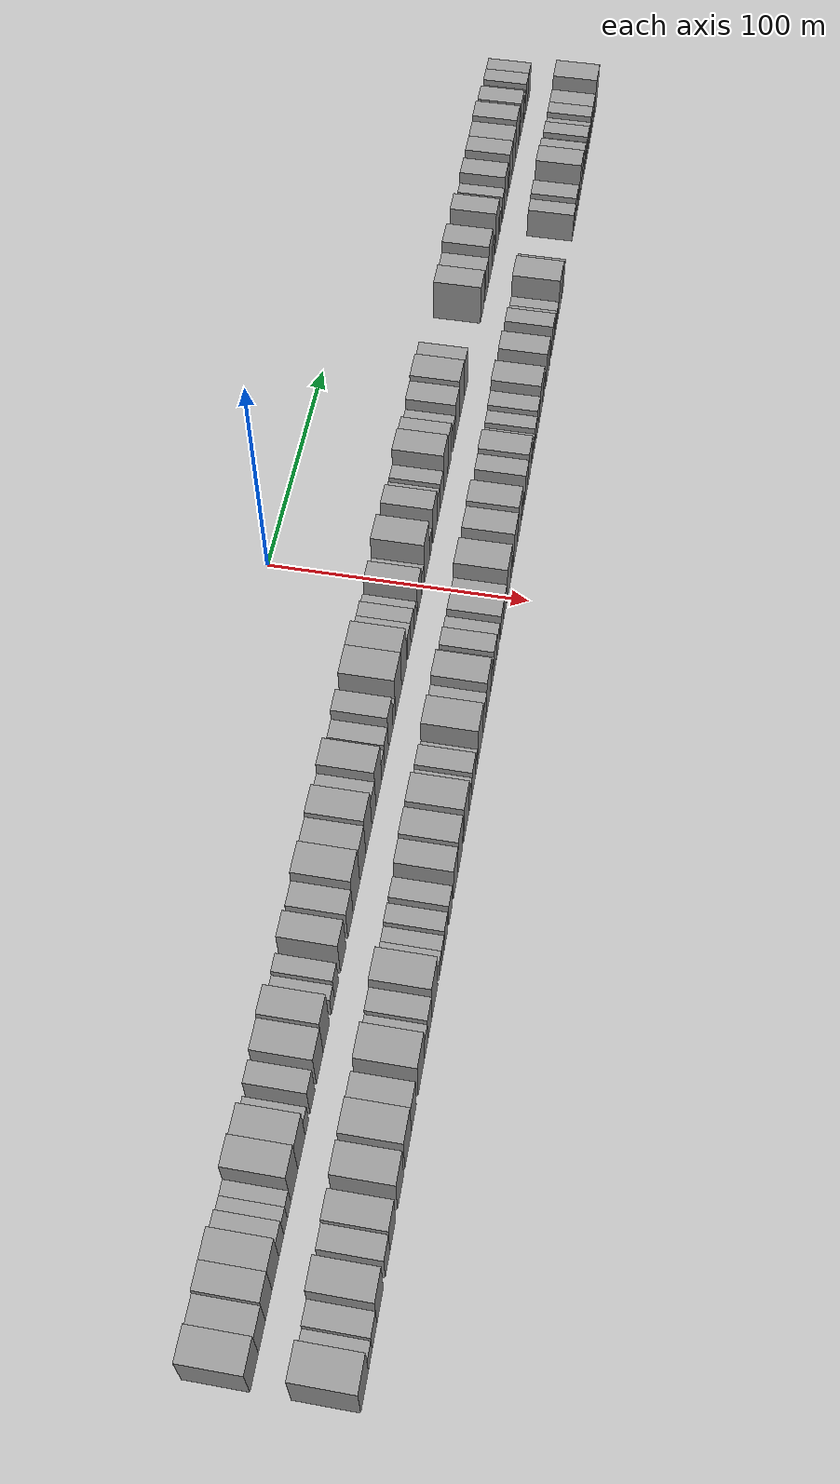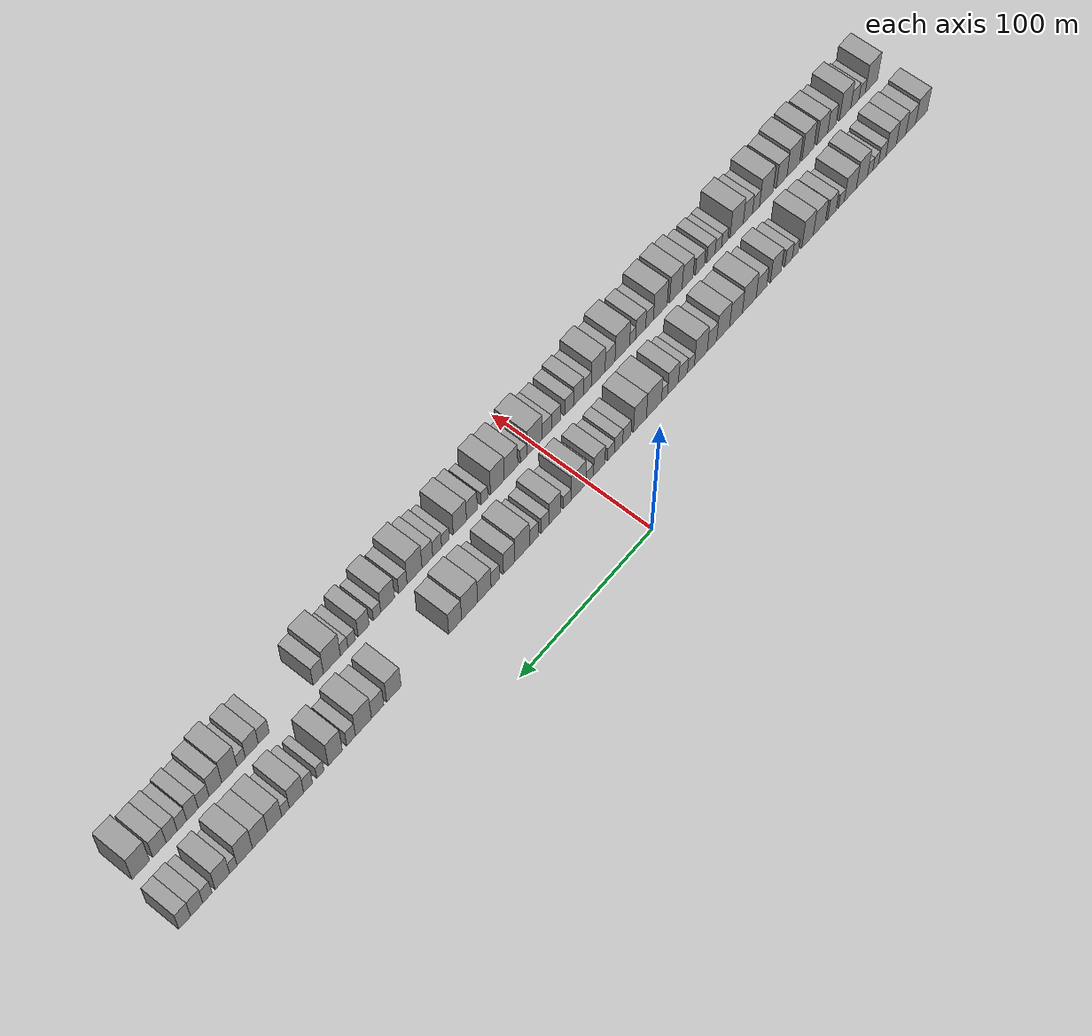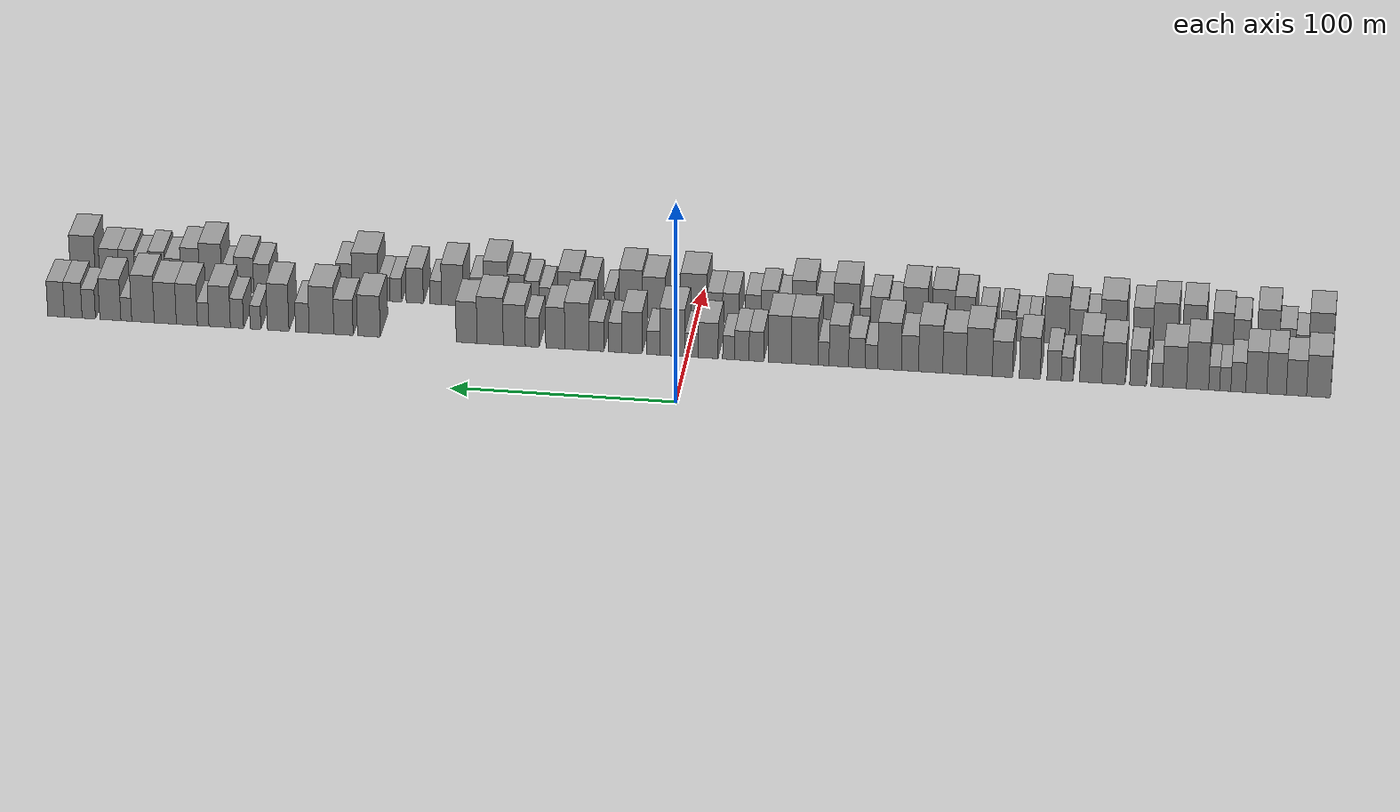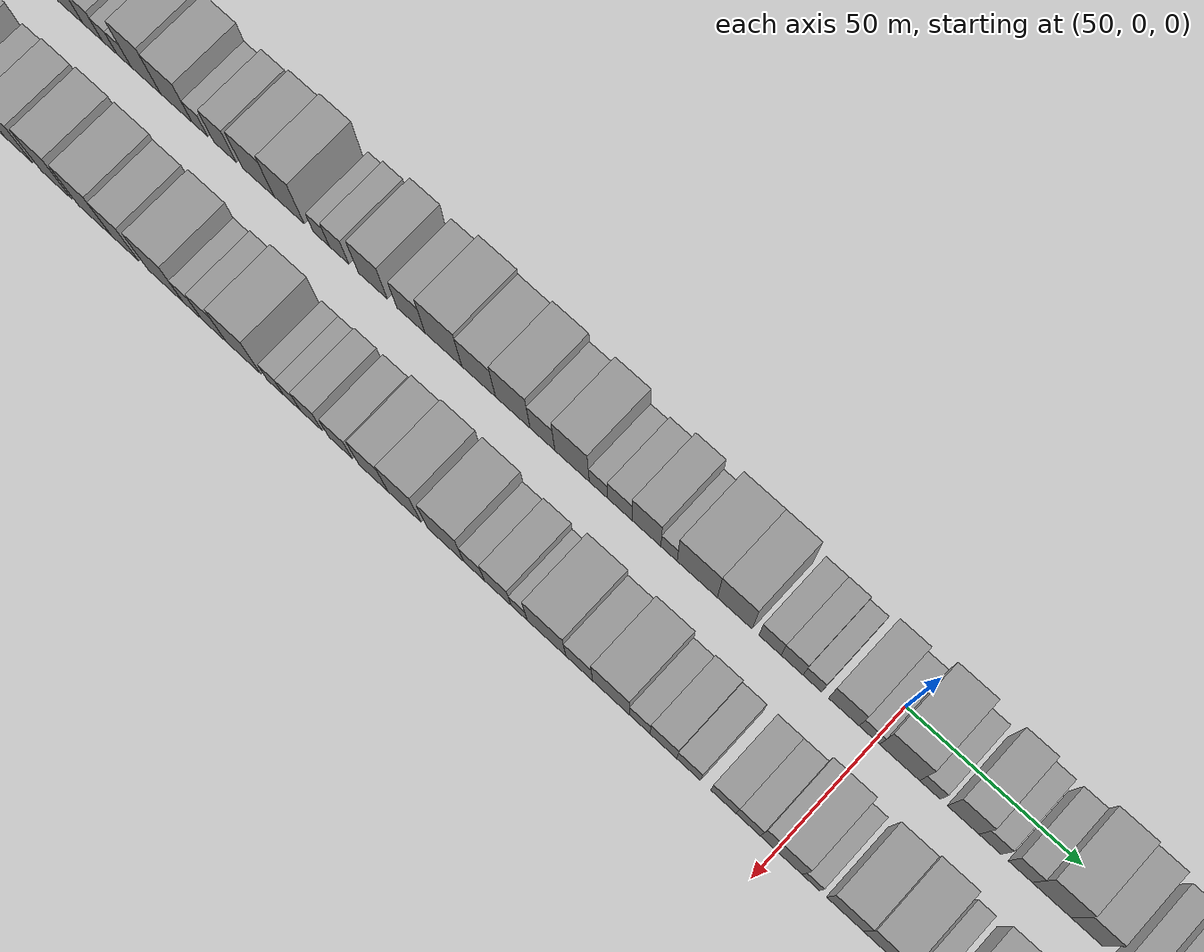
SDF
<sdf version="1.6">
 <world name="default">
  <scene>
   <sky><clouds><speed>12</speed></clouds></sky>
   <ambient>0.4 0.4 0.4 1</ambient>
   <background>0.7 0.7 0.7 1</background>
   <shadows>1</shadows>
  </scene>
  <gravity>0 0 -9.8066</gravity>
  <magnetic_field>6e-06 2.3e-05 -4.2e-05</magnetic_field>
  <physics default="0" name="default_physics" type="ode">
   <ode>
    <solver>
     <type>quick</type>
     <iters>10</iters>
     <sor>1.0</sor>
     <use_dynamic_moi_rescaling>0</use_dynamic_moi_rescaling>
    </solver>
    <constraints>
     <cfm>0</cfm>
     <erp>0.2</erp>
     <contact_max_correcting_vel>100</contact_max_correcting_vel>
     <contact_surface_layer>0.001</contact_surface_layer>
    </constraints>
   </ode>
   <max_step_size>0.004</max_step_size>
   <real_time_factor>1</real_time_factor>
   <real_time_update_rate>250</real_time_update_rate>
  </physics>
  <light name="sun" type="directional">
   <pose>0 0 10 0 0 0</pose>
   <diffuse>0.8 0.8 0.8 1</diffuse>
   <specular>0.2 0.2 0.2 1</specular>
   <attenuation>
    <range>1000</range>
    <constant>0.9</constant>
    <linear>0.01</linear>
    <quadratic>0.001</quadratic>
   </attenuation>
   <direction>-0.5 0.1 -0.9</direction>
  </light>
  <model name="building_1">
   <static>1</static>
   <pose>50.0000 -278.7574 0 0.000000 0.000000 0.000000</pose>
   <link name="link">
    <pose>0 0 10.50 0 0 0</pose>
    <collision name="collision"><geometry><box><size>20.0000 10.4853 21.0000</size></box></geometry></collision>
    <visual name="visual">
     <cast_shadows>0</cast_shadows>
     <geometry><box><size>20.0000 10.4853 21.0000</size></box></geometry>
     <material>
      <script>
       <uri>model://grey_wall/materials/scripts</uri>
       <uri>model://grey_wall/materials/textures</uri>
       <name>vrc/grey_wall</name>
      </script>
     </material>
    </visual>
   </link>
  </model>
  <model name="building_2">
   <static>1</static>
   <pose>50.0000 -269.0719 0 0.000000 0.000000 0.000000</pose>
   <link name="link">
    <pose>0 0 9.00 0 0 0</pose>
    <collision name="collision"><geometry><box><size>20.0000 8.8856 18.0000</size></box></geometry></collision>
    <visual name="visual">
     <cast_shadows>0</cast_shadows>
     <geometry><box><size>20.0000 8.8856 18.0000</size></box></geometry>
     <material>
      <script>
       <uri>model://grey_wall/materials/scripts</uri>
       <uri>model://grey_wall/materials/textures</uri>
       <name>vrc/grey_wall</name>
      </script>
     </material>
    </visual>
   </link>
  </model>
  <model name="building_3">
   <static>1</static>
   <pose>50.0000 -260.3548 0 0.000000 0.000000 0.000000</pose>
   <link name="link">
    <pose>0 0 10.50 0 0 0</pose>
    <collision name="collision"><geometry><box><size>20.0000 8.5487 21.0000</size></box></geometry></collision>
    <visual name="visual">
     <cast_shadows>0</cast_shadows>
     <geometry><box><size>20.0000 8.5487 21.0000</size></box></geometry>
     <material>
      <script>
       <uri>model://grey_wall/materials/scripts</uri>
       <uri>model://grey_wall/materials/textures</uri>
       <name>vrc/grey_wall</name>
      </script>
     </material>
    </visual>
   </link>
  </model>
  <model name="building_4">
   <static>1</static>
   <pose>50.0000 -251.4700 0 0.000000 0.000000 0.000000</pose>
   <link name="link">
    <pose>0 0 10.50 0 0 0</pose>
    <collision name="collision"><geometry><box><size>20.0000 9.2208 21.0000</size></box></geometry></collision>
    <visual name="visual">
     <cast_shadows>0</cast_shadows>
     <geometry><box><size>20.0000 9.2208 21.0000</size></box></geometry>
     <material>
      <script>
       <uri>model://grey_wall/materials/scripts</uri>
       <uri>model://grey_wall/materials/textures</uri>
       <name>vrc/grey_wall</name>
      </script>
     </material>
    </visual>
   </link>
  </model>
  <model name="building_5">
   <static>1</static>
   <pose>50.0000 -243.5951 0 0.000000 0.000000 0.000000</pose>
   <link name="link">
    <pose>0 0 7.50 0 0 0</pose>
    <collision name="collision"><geometry><box><size>20.0000 6.5289 15.0000</size></box></geometry></collision>
    <visual name="visual">
     <cast_shadows>0</cast_shadows>
     <geometry><box><size>20.0000 6.5289 15.0000</size></box></geometry>
     <material>
      <script>
       <uri>model://grey_wall/materials/scripts</uri>
       <uri>model://grey_wall/materials/textures</uri>
       <name>vrc/grey_wall</name>
      </script>
     </material>
    </visual>
   </link>
  </model>
  <model name="building_6">
   <static>1</static>
   <pose>50.0000 -237.8679 0 0.000000 0.000000 0.000000</pose>
   <link name="link">
    <pose>0 0 6.00 0 0 0</pose>
    <collision name="collision"><geometry><box><size>20.0000 4.9256 12.0000</size></box></geometry></collision>
    <visual name="visual">
     <cast_shadows>0</cast_shadows>
     <geometry><box><size>20.0000 4.9256 12.0000</size></box></geometry>
     <material>
      <script>
       <uri>model://grey_wall/materials/scripts</uri>
       <uri>model://grey_wall/materials/textures</uri>
       <name>vrc/grey_wall</name>
      </script>
     </material>
    </visual>
   </link>
  </model>
  <model name="building_7">
   <static>1</static>
   <pose>50.0000 -233.0020 0 0.000000 0.000000 0.000000</pose>
   <link name="link">
    <pose>0 0 6.00 0 0 0</pose>
    <collision name="collision"><geometry><box><size>20.0000 4.8062 12.0000</size></box></geometry></collision>
    <visual name="visual">
     <cast_shadows>0</cast_shadows>
     <geometry><box><size>20.0000 4.8062 12.0000</size></box></geometry>
     <material>
      <script>
       <uri>model://grey_wall/materials/scripts</uri>
       <uri>model://grey_wall/materials/textures</uri>
       <name>vrc/grey_wall</name>
      </script>
     </material>
    </visual>
   </link>
  </model>
  <model name="building_8">
   <static>1</static>
   <pose>50.0000 -225.7242 0 0.000000 0.000000 0.000000</pose>
   <link name="link">
    <pose>0 0 12.00 0 0 0</pose>
    <collision name="collision"><geometry><box><size>20.0000 9.7495 24.0000</size></box></geometry></collision>
    <visual name="visual">
     <cast_shadows>0</cast_shadows>
     <geometry><box><size>20.0000 9.7495 24.0000</size></box></geometry>
     <material>
      <script>
       <uri>model://grey_wall/materials/scripts</uri>
       <uri>model://grey_wall/materials/textures</uri>
       <name>vrc/grey_wall</name>
      </script>
     </material>
    </visual>
   </link>
  </model>
  <model name="building_9">
   <static>1</static>
   <pose>50.0000 -215.6198 0 0.000000 0.000000 0.000000</pose>
   <link name="link">
    <pose>0 0 10.50 0 0 0</pose>
    <collision name="collision"><geometry><box><size>20.0000 10.4592 21.0000</size></box></geometry></collision>
    <visual name="visual">
     <cast_shadows>0</cast_shadows>
     <geometry><box><size>20.0000 10.4592 21.0000</size></box></geometry>
     <material>
      <script>
       <uri>model://grey_wall/materials/scripts</uri>
       <uri>model://grey_wall/materials/textures</uri>
       <name>vrc/grey_wall</name>
      </script>
     </material>
    </visual>
   </link>
  </model>
  <model name="building_10">
   <static>1</static>
   <pose>50.0000 -207.8413 0 0.000000 0.000000 0.000000</pose>
   <link name="link">
    <pose>0 0 6.00 0 0 0</pose>
    <collision name="collision"><geometry><box><size>20.0000 5.0979 12.0000</size></box></geometry></collision>
    <visual name="visual">
     <cast_shadows>0</cast_shadows>
     <geometry><box><size>20.0000 5.0979 12.0000</size></box></geometry>
     <material>
      <script>
       <uri>model://grey_wall/materials/scripts</uri>
       <uri>model://grey_wall/materials/textures</uri>
       <name>vrc/grey_wall</name>
      </script>
     </material>
    </visual>
   </link>
  </model>
  <model name="building_11">
   <static>1</static>
   <pose>50.0000 -199.5938 0 0.000000 0.000000 0.000000</pose>
   <link name="link">
    <pose>0 0 9.00 0 0 0</pose>
    <collision name="collision"><geometry><box><size>20.0000 7.3971 18.0000</size></box></geometry></collision>
    <visual name="visual">
     <cast_shadows>0</cast_shadows>
     <geometry><box><size>20.0000 7.3971 18.0000</size></box></geometry>
     <material>
      <script>
       <uri>model://grey_wall/materials/scripts</uri>
       <uri>model://grey_wall/materials/textures</uri>
       <name>vrc/grey_wall</name>
      </script>
     </material>
    </visual>
   </link>
  </model>
  <model name="building_12">
   <static>1</static>
   <pose>50.0000 -188.7349 0 0.000000 0.000000 0.000000</pose>
   <link name="link">
    <pose>0 0 10.50 0 0 0</pose>
    <collision name="collision"><geometry><box><size>20.0000 10.3207 21.0000</size></box></geometry></collision>
    <visual name="visual">
     <cast_shadows>0</cast_shadows>
     <geometry><box><size>20.0000 10.3207 21.0000</size></box></geometry>
     <material>
      <script>
       <uri>model://grey_wall/materials/scripts</uri>
       <uri>model://grey_wall/materials/textures</uri>
       <name>vrc/grey_wall</name>
      </script>
     </material>
    </visual>
   </link>
  </model>
  <model name="building_13">
   <static>1</static>
   <pose>50.0000 -178.7163 0 0.000000 0.000000 0.000000</pose>
   <link name="link">
    <pose>0 0 12.00 0 0 0</pose>
    <collision name="collision"><geometry><box><size>20.0000 9.7165 24.0000</size></box></geometry></collision>
    <visual name="visual">
     <cast_shadows>0</cast_shadows>
     <geometry><box><size>20.0000 9.7165 24.0000</size></box></geometry>
     <material>
      <script>
       <uri>model://grey_wall/materials/scripts</uri>
       <uri>model://grey_wall/materials/textures</uri>
       <name>vrc/grey_wall</name>
      </script>
     </material>
    </visual>
   </link>
  </model>
  <model name="building_14">
   <static>1</static>
   <pose>50.0000 -168.2957 0 0.000000 0.000000 0.000000</pose>
   <link name="link">
    <pose>0 0 6.00 0 0 0</pose>
    <collision name="collision"><geometry><box><size>20.0000 5.1247 12.0000</size></box></geometry></collision>
    <visual name="visual">
     <cast_shadows>0</cast_shadows>
     <geometry><box><size>20.0000 5.1247 12.0000</size></box></geometry>
     <material>
      <script>
       <uri>model://grey_wall/materials/scripts</uri>
       <uri>model://grey_wall/materials/textures</uri>
       <name>vrc/grey_wall</name>
      </script>
     </material>
    </visual>
   </link>
  </model>
  <model name="building_15">
   <static>1</static>
   <pose>50.0000 -162.6026 0 0.000000 0.000000 0.000000</pose>
   <link name="link">
    <pose>0 0 7.50 0 0 0</pose>
    <collision name="collision"><geometry><box><size>20.0000 6.2617 15.0000</size></box></geometry></collision>
    <visual name="visual">
     <cast_shadows>0</cast_shadows>
     <geometry><box><size>20.0000 6.2617 15.0000</size></box></geometry>
     <material>
      <script>
       <uri>model://grey_wall/materials/scripts</uri>
       <uri>model://grey_wall/materials/textures</uri>
       <name>vrc/grey_wall</name>
      </script>
     </material>
    </visual>
   </link>
  </model>
  <model name="building_16">
   <static>1</static>
   <pose>50.0000 -151.8582 0 0.000000 0.000000 0.000000</pose>
   <link name="link">
    <pose>0 0 10.50 0 0 0</pose>
    <collision name="collision"><geometry><box><size>20.0000 9.2272 21.0000</size></box></geometry></collision>
    <visual name="visual">
     <cast_shadows>0</cast_shadows>
     <geometry><box><size>20.0000 9.2272 21.0000</size></box></geometry>
     <material>
      <script>
       <uri>model://grey_wall/materials/scripts</uri>
       <uri>model://grey_wall/materials/textures</uri>
       <name>vrc/grey_wall</name>
      </script>
     </material>
    </visual>
   </link>
  </model>
  <model name="building_17">
   <static>1</static>
   <pose>50.0000 -139.7778 0 0.000000 0.000000 0.000000</pose>
   <link name="link">
    <pose>0 0 9.00 0 0 0</pose>
    <collision name="collision"><geometry><box><size>20.0000 8.9334 18.0000</size></box></geometry></collision>
    <visual name="visual">
     <cast_shadows>0</cast_shadows>
     <geometry><box><size>20.0000 8.9334 18.0000</size></box></geometry>
     <material>
      <script>
       <uri>model://grey_wall/materials/scripts</uri>
       <uri>model://grey_wall/materials/textures</uri>
       <name>vrc/grey_wall</name>
      </script>
     </material>
    </visual>
   </link>
  </model>
  <model name="building_18">
   <static>1</static>
   <pose>50.0000 -129.5712 0 0.000000 0.000000 0.000000</pose>
   <link name="link">
    <pose>0 0 12.00 0 0 0</pose>
    <collision name="collision"><geometry><box><size>20.0000 11.4799 24.0000</size></box></geometry></collision>
    <visual name="visual">
     <cast_shadows>0</cast_shadows>
     <geometry><box><size>20.0000 11.4799 24.0000</size></box></geometry>
     <material>
      <script>
       <uri>model://grey_wall/materials/scripts</uri>
       <uri>model://grey_wall/materials/textures</uri>
       <name>vrc/grey_wall</name>
      </script>
     </material>
    </visual>
   </link>
  </model>
  <model name="building_19">
   <static>1</static>
   <pose>50.0000 -118.5897 0 0.000000 0.000000 0.000000</pose>
   <link name="link">
    <pose>0 0 10.50 0 0 0</pose>
    <collision name="collision"><geometry><box><size>20.0000 10.4830 21.0000</size></box></geometry></collision>
    <visual name="visual">
     <cast_shadows>0</cast_shadows>
     <geometry><box><size>20.0000 10.4830 21.0000</size></box></geometry>
     <material>
      <script>
       <uri>model://grey_wall/materials/scripts</uri>
       <uri>model://grey_wall/materials/textures</uri>
       <name>vrc/grey_wall</name>
      </script>
     </material>
    </visual>
   </link>
  </model>
  <model name="building_20">
   <static>1</static>
   <pose>50.0000 -107.9969 0 0.000000 0.000000 0.000000</pose>
   <link name="link">
    <pose>0 0 12.00 0 0 0</pose>
    <collision name="collision"><geometry><box><size>20.0000 10.7027 24.0000</size></box></geometry></collision>
    <visual name="visual">
     <cast_shadows>0</cast_shadows>
     <geometry><box><size>20.0000 10.7027 24.0000</size></box></geometry>
     <material>
      <script>
       <uri>model://grey_wall/materials/scripts</uri>
       <uri>model://grey_wall/materials/textures</uri>
       <name>vrc/grey_wall</name>
      </script>
     </material>
    </visual>
   </link>
  </model>
  <model name="building_21">
   <static>1</static>
   <pose>50.0000 -98.8273 0 0.000000 0.000000 0.000000</pose>
   <link name="link">
    <pose>0 0 9.00 0 0 0</pose>
    <collision name="collision"><geometry><box><size>20.0000 7.6364 18.0000</size></box></geometry></collision>
    <visual name="visual">
     <cast_shadows>0</cast_shadows>
     <geometry><box><size>20.0000 7.6364 18.0000</size></box></geometry>
     <material>
      <script>
       <uri>model://grey_wall/materials/scripts</uri>
       <uri>model://grey_wall/materials/textures</uri>
       <name>vrc/grey_wall</name>
      </script>
     </material>
    </visual>
   </link>
  </model>
  <model name="building_22">
   <static>1</static>
   <pose>50.0000 -89.7715 0 0.000000 0.000000 0.000000</pose>
   <link name="link">
    <pose>0 0 12.00 0 0 0</pose>
    <collision name="collision"><geometry><box><size>20.0000 10.4751 24.0000</size></box></geometry></collision>
    <visual name="visual">
     <cast_shadows>0</cast_shadows>
     <geometry><box><size>20.0000 10.4751 24.0000</size></box></geometry>
     <material>
      <script>
       <uri>model://grey_wall/materials/scripts</uri>
       <uri>model://grey_wall/materials/textures</uri>
       <name>vrc/grey_wall</name>
      </script>
     </material>
    </visual>
   </link>
  </model>
  <model name="building_23">
   <static>1</static>
   <pose>50.0000 -81.7449 0 0.000000 0.000000 0.000000</pose>
   <link name="link">
    <pose>0 0 6.00 0 0 0</pose>
    <collision name="collision"><geometry><box><size>20.0000 5.5781 12.0000</size></box></geometry></collision>
    <visual name="visual">
     <cast_shadows>0</cast_shadows>
     <geometry><box><size>20.0000 5.5781 12.0000</size></box></geometry>
     <material>
      <script>
       <uri>model://grey_wall/materials/scripts</uri>
       <uri>model://grey_wall/materials/textures</uri>
       <name>vrc/grey_wall</name>
      </script>
     </material>
    </visual>
   </link>
  </model>
  <model name="building_24">
   <static>1</static>
   <pose>50.0000 -75.2791 0 0.000000 0.000000 0.000000</pose>
   <link name="link">
    <pose>0 0 7.50 0 0 0</pose>
    <collision name="collision"><geometry><box><size>20.0000 7.3536 15.0000</size></box></geometry></collision>
    <visual name="visual">
     <cast_shadows>0</cast_shadows>
     <geometry><box><size>20.0000 7.3536 15.0000</size></box></geometry>
     <material>
      <script>
       <uri>model://grey_wall/materials/scripts</uri>
       <uri>model://grey_wall/materials/textures</uri>
       <name>vrc/grey_wall</name>
      </script>
     </material>
    </visual>
   </link>
  </model>
  <model name="building_25">
   <static>1</static>
   <pose>50.0000 -67.2632 0 0.000000 0.000000 0.000000</pose>
   <link name="link">
    <pose>0 0 10.50 0 0 0</pose>
    <collision name="collision"><geometry><box><size>20.0000 8.6782 21.0000</size></box></geometry></collision>
    <visual name="visual">
     <cast_shadows>0</cast_shadows>
     <geometry><box><size>20.0000 8.6782 21.0000</size></box></geometry>
     <material>
      <script>
       <uri>model://grey_wall/materials/scripts</uri>
       <uri>model://grey_wall/materials/textures</uri>
       <name>vrc/grey_wall</name>
      </script>
     </material>
    </visual>
   </link>
  </model>
  <model name="building_26">
   <static>1</static>
   <pose>50.0000 -60.4848 0 0.000000 0.000000 0.000000</pose>
   <link name="link">
    <pose>0 0 6.00 0 0 0</pose>
    <collision name="collision"><geometry><box><size>20.0000 4.8786 12.0000</size></box></geometry></collision>
    <visual name="visual">
     <cast_shadows>0</cast_shadows>
     <geometry><box><size>20.0000 4.8786 12.0000</size></box></geometry>
     <material>
      <script>
       <uri>model://grey_wall/materials/scripts</uri>
       <uri>model://grey_wall/materials/textures</uri>
       <name>vrc/grey_wall</name>
      </script>
     </material>
    </visual>
   </link>
  </model>
  <model name="building_27">
   <static>1</static>
   <pose>50.0000 -52.0567 0 0.000000 0.000000 0.000000</pose>
   <link name="link">
    <pose>0 0 12.00 0 0 0</pose>
    <collision name="collision"><geometry><box><size>20.0000 11.9777 24.0000</size></box></geometry></collision>
    <visual name="visual">
     <cast_shadows>0</cast_shadows>
     <geometry><box><size>20.0000 11.9777 24.0000</size></box></geometry>
     <material>
      <script>
       <uri>model://grey_wall/materials/scripts</uri>
       <uri>model://grey_wall/materials/textures</uri>
       <name>vrc/grey_wall</name>
      </script>
     </material>
    </visual>
   </link>
  </model>
  <model name="building_28">
   <static>1</static>
   <pose>50.0000 -40.9466 0 0.000000 0.000000 0.000000</pose>
   <link name="link">
    <pose>0 0 12.00 0 0 0</pose>
    <collision name="collision"><geometry><box><size>20.0000 10.2426 24.0000</size></box></geometry></collision>
    <visual name="visual">
     <cast_shadows>0</cast_shadows>
     <geometry><box><size>20.0000 10.2426 24.0000</size></box></geometry>
     <material>
      <script>
       <uri>model://grey_wall/materials/scripts</uri>
       <uri>model://grey_wall/materials/textures</uri>
       <name>vrc/grey_wall</name>
      </script>
     </material>
    </visual>
   </link>
  </model>
  <model name="building_29">
   <static>1</static>
   <pose>50.0000 -30.5778 0 0.000000 0.000000 0.000000</pose>
   <link name="link">
    <pose>0 0 7.50 0 0 0</pose>
    <collision name="collision"><geometry><box><size>20.0000 6.4950 15.0000</size></box></geometry></collision>
    <visual name="visual">
     <cast_shadows>0</cast_shadows>
     <geometry><box><size>20.0000 6.4950 15.0000</size></box></geometry>
     <material>
      <script>
       <uri>model://grey_wall/materials/scripts</uri>
       <uri>model://grey_wall/materials/textures</uri>
       <name>vrc/grey_wall</name>
      </script>
     </material>
    </visual>
   </link>
  </model>
  <model name="building_30">
   <static>1</static>
   <pose>50.0000 -24.1028 0 0.000000 0.000000 0.000000</pose>
   <link name="link">
    <pose>0 0 7.50 0 0 0</pose>
    <collision name="collision"><geometry><box><size>20.0000 6.4550 15.0000</size></box></geometry></collision>
    <visual name="visual">
     <cast_shadows>0</cast_shadows>
     <geometry><box><size>20.0000 6.4550 15.0000</size></box></geometry>
     <material>
      <script>
       <uri>model://grey_wall/materials/scripts</uri>
       <uri>model://grey_wall/materials/textures</uri>
       <name>vrc/grey_wall</name>
      </script>
     </material>
    </visual>
   </link>
  </model>
  <model name="building_31">
   <static>1</static>
   <pose>50.0000 -18.1792 0 0.000000 0.000000 0.000000</pose>
   <link name="link">
    <pose>0 0 6.00 0 0 0</pose>
    <collision name="collision"><geometry><box><size>20.0000 5.3922 12.0000</size></box></geometry></collision>
    <visual name="visual">
     <cast_shadows>0</cast_shadows>
     <geometry><box><size>20.0000 5.3922 12.0000</size></box></geometry>
     <material>
      <script>
       <uri>model://grey_wall/materials/scripts</uri>
       <uri>model://grey_wall/materials/textures</uri>
       <name>vrc/grey_wall</name>
      </script>
     </material>
    </visual>
   </link>
  </model>
  <model name="building_32">
   <static>1</static>
   <pose>50.0000 -9.0547 0 0.000000 0.000000 0.000000</pose>
   <link name="link">
    <pose>0 0 9.00 0 0 0</pose>
    <collision name="collision"><geometry><box><size>20.0000 8.8566 18.0000</size></box></geometry></collision>
    <visual name="visual">
     <cast_shadows>0</cast_shadows>
     <geometry><box><size>20.0000 8.8566 18.0000</size></box></geometry>
     <material>
      <script>
       <uri>model://grey_wall/materials/scripts</uri>
       <uri>model://grey_wall/materials/textures</uri>
       <name>vrc/grey_wall</name>
      </script>
     </material>
    </visual>
   </link>
  </model>
  <model name="building_33">
   <static>1</static>
   <pose>50.0000 -1.6798 0 0.000000 0.000000 0.000000</pose>
   <link name="link">
    <pose>0 0 6.00 0 0 0</pose>
    <collision name="collision"><geometry><box><size>20.0000 5.8933 12.0000</size></box></geometry></collision>
    <visual name="visual">
     <cast_shadows>0</cast_shadows>
     <geometry><box><size>20.0000 5.8933 12.0000</size></box></geometry>
     <material>
      <script>
       <uri>model://grey_wall/materials/scripts</uri>
       <uri>model://grey_wall/materials/textures</uri>
       <name>vrc/grey_wall</name>
      </script>
     </material>
    </visual>
   </link>
  </model>
  <model name="building_34">
   <static>1</static>
   <pose>50.0000 6.9483 0 0.000000 0.000000 0.000000</pose>
   <link name="link">
    <pose>0 0 12.00 0 0 0</pose>
    <collision name="collision"><geometry><box><size>20.0000 11.3630 24.0000</size></box></geometry></collision>
    <visual name="visual">
     <cast_shadows>0</cast_shadows>
     <geometry><box><size>20.0000 11.3630 24.0000</size></box></geometry>
     <material>
      <script>
       <uri>model://grey_wall/materials/scripts</uri>
       <uri>model://grey_wall/materials/textures</uri>
       <name>vrc/grey_wall</name>
      </script>
     </material>
    </visual>
   </link>
  </model>
  <model name="building_35">
   <static>1</static>
   <pose>50.0000 15.5650 0 0.000000 0.000000 0.000000</pose>
   <link name="link">
    <pose>0 0 6.00 0 0 0</pose>
    <collision name="collision"><geometry><box><size>20.0000 5.8705 12.0000</size></box></geometry></collision>
    <visual name="visual">
     <cast_shadows>0</cast_shadows>
     <geometry><box><size>20.0000 5.8705 12.0000</size></box></geometry>
     <material>
      <script>
       <uri>model://grey_wall/materials/scripts</uri>
       <uri>model://grey_wall/materials/textures</uri>
       <name>vrc/grey_wall</name>
      </script>
     </material>
    </visual>
   </link>
  </model>
  <model name="building_36">
   <static>1</static>
   <pose>50.0000 24.9754 0 0.000000 0.000000 0.000000</pose>
   <link name="link">
    <pose>0 0 10.50 0 0 0</pose>
    <collision name="collision"><geometry><box><size>20.0000 8.9502 21.0000</size></box></geometry></collision>
    <visual name="visual">
     <cast_shadows>0</cast_shadows>
     <geometry><box><size>20.0000 8.9502 21.0000</size></box></geometry>
     <material>
      <script>
       <uri>model://grey_wall/materials/scripts</uri>
       <uri>model://grey_wall/materials/textures</uri>
       <name>vrc/grey_wall</name>
      </script>
     </material>
    </visual>
   </link>
  </model>
  <model name="building_37">
   <static>1</static>
   <pose>50.0000 32.5412 0 0.000000 0.000000 0.000000</pose>
   <link name="link">
    <pose>0 0 7.50 0 0 0</pose>
    <collision name="collision"><geometry><box><size>20.0000 6.1814 15.0000</size></box></geometry></collision>
    <visual name="visual">
     <cast_shadows>0</cast_shadows>
     <geometry><box><size>20.0000 6.1814 15.0000</size></box></geometry>
     <material>
      <script>
       <uri>model://grey_wall/materials/scripts</uri>
       <uri>model://grey_wall/materials/textures</uri>
       <name>vrc/grey_wall</name>
      </script>
     </material>
    </visual>
   </link>
  </model>
  <model name="building_38">
   <static>1</static>
   <pose>50.0000 40.9875 0 0.000000 0.000000 0.000000</pose>
   <link name="link">
    <pose>0 0 7.50 0 0 0</pose>
    <collision name="collision"><geometry><box><size>20.0000 6.7112 15.0000</size></box></geometry></collision>
    <visual name="visual">
     <cast_shadows>0</cast_shadows>
     <geometry><box><size>20.0000 6.7112 15.0000</size></box></geometry>
     <material>
      <script>
       <uri>model://grey_wall/materials/scripts</uri>
       <uri>model://grey_wall/materials/textures</uri>
       <name>vrc/grey_wall</name>
      </script>
     </material>
    </visual>
   </link>
  </model>
  <model name="building_39">
   <static>1</static>
   <pose>50.0000 49.7441 0 0.000000 0.000000 0.000000</pose>
   <link name="link">
    <pose>0 0 12.00 0 0 0</pose>
    <collision name="collision"><geometry><box><size>20.0000 10.8022 24.0000</size></box></geometry></collision>
    <visual name="visual">
     <cast_shadows>0</cast_shadows>
     <geometry><box><size>20.0000 10.8022 24.0000</size></box></geometry>
     <material>
      <script>
       <uri>model://grey_wall/materials/scripts</uri>
       <uri>model://grey_wall/materials/textures</uri>
       <name>vrc/grey_wall</name>
      </script>
     </material>
    </visual>
   </link>
  </model>
  <model name="building_40">
   <static>1</static>
   <pose>50.0000 59.4152 0 0.000000 0.000000 0.000000</pose>
   <link name="link">
    <pose>0 0 10.50 0 0 0</pose>
    <collision name="collision"><geometry><box><size>20.0000 8.5400 21.0000</size></box></geometry></collision>
    <visual name="visual">
     <cast_shadows>0</cast_shadows>
     <geometry><box><size>20.0000 8.5400 21.0000</size></box></geometry>
     <material>
      <script>
       <uri>model://grey_wall/materials/scripts</uri>
       <uri>model://grey_wall/materials/textures</uri>
       <name>vrc/grey_wall</name>
      </script>
     </material>
    </visual>
   </link>
  </model>
  <model name="building_41">
   <static>1</static>
   <pose>50.0000 69.7867 0 0.000000 0.000000 0.000000</pose>
   <link name="link">
    <pose>0 0 7.50 0 0 0</pose>
    <collision name="collision"><geometry><box><size>20.0000 6.2029 15.0000</size></box></geometry></collision>
    <visual name="visual">
     <cast_shadows>0</cast_shadows>
     <geometry><box><size>20.0000 6.2029 15.0000</size></box></geometry>
     <material>
      <script>
       <uri>model://grey_wall/materials/scripts</uri>
       <uri>model://grey_wall/materials/textures</uri>
       <name>vrc/grey_wall</name>
      </script>
     </material>
    </visual>
   </link>
  </model>
  <model name="building_42">
   <static>1</static>
   <pose>50.0000 77.8425 0 0.000000 0.000000 0.000000</pose>
   <link name="link">
    <pose>0 0 10.50 0 0 0</pose>
    <collision name="collision"><geometry><box><size>20.0000 9.9086 21.0000</size></box></geometry></collision>
    <visual name="visual">
     <cast_shadows>0</cast_shadows>
     <geometry><box><size>20.0000 9.9086 21.0000</size></box></geometry>
     <material>
      <script>
       <uri>model://grey_wall/materials/scripts</uri>
       <uri>model://grey_wall/materials/textures</uri>
       <name>vrc/grey_wall</name>
      </script>
     </material>
    </visual>
   </link>
  </model>
  <model name="building_43">
   <static>1</static>
   <pose>50.0000 88.6916 0 0.000000 0.000000 0.000000</pose>
   <link name="link">
    <pose>0 0 12.00 0 0 0</pose>
    <collision name="collision"><geometry><box><size>20.0000 11.7896 24.0000</size></box></geometry></collision>
    <visual name="visual">
     <cast_shadows>0</cast_shadows>
     <geometry><box><size>20.0000 11.7896 24.0000</size></box></geometry>
     <material>
      <script>
       <uri>model://grey_wall/materials/scripts</uri>
       <uri>model://grey_wall/materials/textures</uri>
       <name>vrc/grey_wall</name>
      </script>
     </material>
    </visual>
   </link>
  </model>
  <model name="building_44">
   <static>1</static>
   <pose>50.0000 99.2791 0 0.000000 0.000000 0.000000</pose>
   <link name="link">
    <pose>0 0 10.50 0 0 0</pose>
    <collision name="collision"><geometry><box><size>20.0000 9.3855 21.0000</size></box></geometry></collision>
    <visual name="visual">
     <cast_shadows>0</cast_shadows>
     <geometry><box><size>20.0000 9.3855 21.0000</size></box></geometry>
     <material>
      <script>
       <uri>model://grey_wall/materials/scripts</uri>
       <uri>model://grey_wall/materials/textures</uri>
       <name>vrc/grey_wall</name>
      </script>
     </material>
    </visual>
   </link>
  </model>
  <model name="building_45">
   <static>1</static>
   <pose>50.0000 143.3644 0 0.000000 0.000000 0.000000</pose>
   <link name="link">
    <pose>0 0 10.50 0 0 0</pose>
    <collision name="collision"><geometry><box><size>20.0000 10.2617 21.0000</size></box></geometry></collision>
    <visual name="visual">
     <cast_shadows>0</cast_shadows>
     <geometry><box><size>20.0000 10.2617 21.0000</size></box></geometry>
     <material>
      <script>
       <uri>model://grey_wall/materials/scripts</uri>
       <uri>model://grey_wall/materials/textures</uri>
       <name>vrc/grey_wall</name>
      </script>
     </material>
    </visual>
   </link>
  </model>
  <model name="building_46">
   <static>1</static>
   <pose>50.0000 154.8397 0 0.000000 0.000000 0.000000</pose>
   <link name="link">
    <pose>0 0 9.00 0 0 0</pose>
    <collision name="collision"><geometry><box><size>20.0000 8.6888 18.0000</size></box></geometry></collision>
    <visual name="visual">
     <cast_shadows>0</cast_shadows>
     <geometry><box><size>20.0000 8.6888 18.0000</size></box></geometry>
     <material>
      <script>
       <uri>model://grey_wall/materials/scripts</uri>
       <uri>model://grey_wall/materials/textures</uri>
       <name>vrc/grey_wall</name>
      </script>
     </material>
    </visual>
   </link>
  </model>
  <model name="building_47">
   <static>1</static>
   <pose>50.0000 164.7702 0 0.000000 0.000000 0.000000</pose>
   <link name="link">
    <pose>0 0 12.00 0 0 0</pose>
    <collision name="collision"><geometry><box><size>20.0000 11.1723 24.0000</size></box></geometry></collision>
    <visual name="visual">
     <cast_shadows>0</cast_shadows>
     <geometry><box><size>20.0000 11.1723 24.0000</size></box></geometry>
     <material>
      <script>
       <uri>model://grey_wall/materials/scripts</uri>
       <uri>model://grey_wall/materials/textures</uri>
       <name>vrc/grey_wall</name>
      </script>
     </material>
    </visual>
   </link>
  </model>
  <model name="building_48">
   <static>1</static>
   <pose>50.0000 173.4471 0 0.000000 0.000000 0.000000</pose>
   <link name="link">
    <pose>0 0 7.50 0 0 0</pose>
    <collision name="collision"><geometry><box><size>20.0000 6.1817 15.0000</size></box></geometry></collision>
    <visual name="visual">
     <cast_shadows>0</cast_shadows>
     <geometry><box><size>20.0000 6.1817 15.0000</size></box></geometry>
     <material>
      <script>
       <uri>model://grey_wall/materials/scripts</uri>
       <uri>model://grey_wall/materials/textures</uri>
       <name>vrc/grey_wall</name>
      </script>
     </material>
    </visual>
   </link>
  </model>
  <model name="building_49">
   <static>1</static>
   <pose>50.0000 184.4023 0 0.000000 0.000000 0.000000</pose>
   <link name="link">
    <pose>0 0 12.00 0 0 0</pose>
    <collision name="collision"><geometry><box><size>20.0000 9.7286 24.0000</size></box></geometry></collision>
    <visual name="visual">
     <cast_shadows>0</cast_shadows>
     <geometry><box><size>20.0000 9.7286 24.0000</size></box></geometry>
     <material>
      <script>
       <uri>model://grey_wall/materials/scripts</uri>
       <uri>model://grey_wall/materials/textures</uri>
       <name>vrc/grey_wall</name>
      </script>
     </material>
    </visual>
   </link>
  </model>
  <model name="building_50">
   <static>1</static>
   <pose>50.0000 194.6865 0 0.000000 0.000000 0.000000</pose>
   <link name="link">
    <pose>0 0 6.00 0 0 0</pose>
    <collision name="collision"><geometry><box><size>20.0000 4.8399 12.0000</size></box></geometry></collision>
    <visual name="visual">
     <cast_shadows>0</cast_shadows>
     <geometry><box><size>20.0000 4.8399 12.0000</size></box></geometry>
     <material>
      <script>
       <uri>model://grey_wall/materials/scripts</uri>
       <uri>model://grey_wall/materials/textures</uri>
       <name>vrc/grey_wall</name>
      </script>
     </material>
    </visual>
   </link>
  </model>
  <model name="building_51">
   <static>1</static>
   <pose>50.0000 203.1136 0 0.000000 0.000000 0.000000</pose>
   <link name="link">
    <pose>0 0 7.50 0 0 0</pose>
    <collision name="collision"><geometry><box><size>20.0000 6.0143 15.0000</size></box></geometry></collision>
    <visual name="visual">
     <cast_shadows>0</cast_shadows>
     <geometry><box><size>20.0000 6.0143 15.0000</size></box></geometry>
     <material>
      <script>
       <uri>model://grey_wall/materials/scripts</uri>
       <uri>model://grey_wall/materials/textures</uri>
       <name>vrc/grey_wall</name>
      </script>
     </material>
    </visual>
   </link>
  </model>
  <model name="building_52">
   <static>1</static>
   <pose>50.0000 210.9976 0 0.000000 0.000000 0.000000</pose>
   <link name="link">
    <pose>0 0 10.50 0 0 0</pose>
    <collision name="collision"><geometry><box><size>20.0000 9.7535 21.0000</size></box></geometry></collision>
    <visual name="visual">
     <cast_shadows>0</cast_shadows>
     <geometry><box><size>20.0000 9.7535 21.0000</size></box></geometry>
     <material>
      <script>
       <uri>model://grey_wall/materials/scripts</uri>
       <uri>model://grey_wall/materials/textures</uri>
       <name>vrc/grey_wall</name>
      </script>
     </material>
    </visual>
   </link>
  </model>
  <model name="building_53">
   <static>1</static>
   <pose>50.0000 218.4777 0 0.000000 0.000000 0.000000</pose>
   <link name="link">
    <pose>0 0 6.00 0 0 0</pose>
    <collision name="collision"><geometry><box><size>20.0000 5.2067 12.0000</size></box></geometry></collision>
    <visual name="visual">
     <cast_shadows>0</cast_shadows>
     <geometry><box><size>20.0000 5.2067 12.0000</size></box></geometry>
     <material>
      <script>
       <uri>model://grey_wall/materials/scripts</uri>
       <uri>model://grey_wall/materials/textures</uri>
       <name>vrc/grey_wall</name>
      </script>
     </material>
    </visual>
   </link>
  </model>
  <model name="building_54">
   <static>1</static>
   <pose>50.0000 225.8662 0 0.000000 0.000000 0.000000</pose>
   <link name="link">
    <pose>0 0 10.50 0 0 0</pose>
    <collision name="collision"><geometry><box><size>20.0000 9.5703 21.0000</size></box></geometry></collision>
    <visual name="visual">
     <cast_shadows>0</cast_shadows>
     <geometry><box><size>20.0000 9.5703 21.0000</size></box></geometry>
     <material>
      <script>
       <uri>model://grey_wall/materials/scripts</uri>
       <uri>model://grey_wall/materials/textures</uri>
       <name>vrc/grey_wall</name>
      </script>
     </material>
    </visual>
   </link>
  </model>
  <model name="building_55">
   <static>1</static>
   <pose>50.0000 235.6811 0 0.000000 0.000000 0.000000</pose>
   <link name="link">
    <pose>0 0 10.50 0 0 0</pose>
    <collision name="collision"><geometry><box><size>20.0000 10.0596 21.0000</size></box></geometry></collision>
    <visual name="visual">
     <cast_shadows>0</cast_shadows>
     <geometry><box><size>20.0000 10.0596 21.0000</size></box></geometry>
     <material>
      <script>
       <uri>model://grey_wall/materials/scripts</uri>
       <uri>model://grey_wall/materials/textures</uri>
       <name>vrc/grey_wall</name>
      </script>
     </material>
    </visual>
   </link>
  </model>
  <model name="building_56">
   <static>1</static>
   <pose>50.0000 245.8438 0 0.000000 0.000000 0.000000</pose>
   <link name="link">
    <pose>0 0 12.00 0 0 0</pose>
    <collision name="collision"><geometry><box><size>20.0000 10.2658 24.0000</size></box></geometry></collision>
    <visual name="visual">
     <cast_shadows>0</cast_shadows>
     <geometry><box><size>20.0000 10.2658 24.0000</size></box></geometry>
     <material>
      <script>
       <uri>model://grey_wall/materials/scripts</uri>
       <uri>model://grey_wall/materials/textures</uri>
       <name>vrc/grey_wall</name>
      </script>
     </material>
    </visual>
   </link>
  </model>
  <model name="building_57">
   <static>1</static>
   <pose>50.0000 253.4522 0 0.000000 0.000000 0.000000</pose>
   <link name="link">
    <pose>0 0 6.00 0 0 0</pose>
    <collision name="collision"><geometry><box><size>20.0000 4.9509 12.0000</size></box></geometry></collision>
    <visual name="visual">
     <cast_shadows>0</cast_shadows>
     <geometry><box><size>20.0000 4.9509 12.0000</size></box></geometry>
     <material>
      <script>
       <uri>model://grey_wall/materials/scripts</uri>
       <uri>model://grey_wall/materials/textures</uri>
       <name>vrc/grey_wall</name>
      </script>
     </material>
    </visual>
   </link>
  </model>
  <model name="building_58">
   <static>1</static>
   <pose>50.0000 260.7237 0 0.000000 0.000000 0.000000</pose>
   <link name="link">
    <pose>0 0 10.50 0 0 0</pose>
    <collision name="collision"><geometry><box><size>20.0000 9.5921 21.0000</size></box></geometry></collision>
    <visual name="visual">
     <cast_shadows>0</cast_shadows>
     <geometry><box><size>20.0000 9.5921 21.0000</size></box></geometry>
     <material>
      <script>
       <uri>model://grey_wall/materials/scripts</uri>
       <uri>model://grey_wall/materials/textures</uri>
       <name>vrc/grey_wall</name>
      </script>
     </material>
    </visual>
   </link>
  </model>
  <model name="building_59">
   <static>1</static>
   <pose>50.0000 270.5678 0 0.000000 0.000000 0.000000</pose>
   <link name="link">
    <pose>0 0 7.50 0 0 0</pose>
    <collision name="collision"><geometry><box><size>20.0000 6.0962 15.0000</size></box></geometry></collision>
    <visual name="visual">
     <cast_shadows>0</cast_shadows>
     <geometry><box><size>20.0000 6.0962 15.0000</size></box></geometry>
     <material>
      <script>
       <uri>model://grey_wall/materials/scripts</uri>
       <uri>model://grey_wall/materials/textures</uri>
       <name>vrc/grey_wall</name>
      </script>
     </material>
    </visual>
   </link>
  </model>
  <model name="building_60">
   <static>1</static>
   <pose>50.0000 277.6173 0 0.000000 0.000000 0.000000</pose>
   <link name="link">
    <pose>0 0 9.00 0 0 0</pose>
    <collision name="collision"><geometry><box><size>20.0000 8.0026 18.0000</size></box></geometry></collision>
    <visual name="visual">
     <cast_shadows>0</cast_shadows>
     <geometry><box><size>20.0000 8.0026 18.0000</size></box></geometry>
     <material>
      <script>
       <uri>model://grey_wall/materials/scripts</uri>
       <uri>model://grey_wall/materials/textures</uri>
       <name>vrc/grey_wall</name>
      </script>
     </material>
    </visual>
   </link>
  </model>
  <model name="building_61">
   <static>1</static>
   <pose>50.0000 285.4293 0 0.000000 0.000000 0.000000</pose>
   <link name="link">
    <pose>0 0 9.00 0 0 0</pose>
    <collision name="collision"><geometry><box><size>20.0000 7.6214 18.0000</size></box></geometry></collision>
    <visual name="visual">
     <cast_shadows>0</cast_shadows>
     <geometry><box><size>20.0000 7.6214 18.0000</size></box></geometry>
     <material>
      <script>
       <uri>model://grey_wall/materials/scripts</uri>
       <uri>model://grey_wall/materials/textures</uri>
       <name>vrc/grey_wall</name>
      </script>
     </material>
    </visual>
   </link>
  </model>
  <model name="building_62">
   <static>1</static>
   <pose>82.0000 -278.5064 0 0.000000 0.000000 0.000000</pose>
   <link name="link">
    <pose>0 0 12.00 0 0 0</pose>
    <collision name="collision"><geometry><box><size>20.0000 10.9872 24.0000</size></box></geometry></collision>
    <visual name="visual">
     <cast_shadows>0</cast_shadows>
     <geometry><box><size>20.0000 10.9872 24.0000</size></box></geometry>
     <material>
      <script>
       <uri>model://grey_wall/materials/scripts</uri>
       <uri>model://grey_wall/materials/textures</uri>
       <name>vrc/grey_wall</name>
      </script>
     </material>
    </visual>
   </link>
  </model>
  <model name="building_63">
   <static>1</static>
   <pose>82.0000 -270.1554 0 0.000000 0.000000 0.000000</pose>
   <link name="link">
    <pose>0 0 6.00 0 0 0</pose>
    <collision name="collision"><geometry><box><size>20.0000 5.7147 12.0000</size></box></geometry></collision>
    <visual name="visual">
     <cast_shadows>0</cast_shadows>
     <geometry><box><size>20.0000 5.7147 12.0000</size></box></geometry>
     <material>
      <script>
       <uri>model://grey_wall/materials/scripts</uri>
       <uri>model://grey_wall/materials/textures</uri>
       <name>vrc/grey_wall</name>
      </script>
     </material>
    </visual>
   </link>
  </model>
  <model name="building_64">
   <static>1</static>
   <pose>82.0000 -263.6507 0 0.000000 0.000000 0.000000</pose>
   <link name="link">
    <pose>0 0 7.50 0 0 0</pose>
    <collision name="collision"><geometry><box><size>20.0000 7.2947 15.0000</size></box></geometry></collision>
    <visual name="visual">
     <cast_shadows>0</cast_shadows>
     <geometry><box><size>20.0000 7.2947 15.0000</size></box></geometry>
     <material>
      <script>
       <uri>model://grey_wall/materials/scripts</uri>
       <uri>model://grey_wall/materials/textures</uri>
       <name>vrc/grey_wall</name>
      </script>
     </material>
    </visual>
   </link>
  </model>
  <model name="building_65">
   <static>1</static>
   <pose>82.0000 -255.0314 0 0.000000 0.000000 0.000000</pose>
   <link name="link">
    <pose>0 0 12.00 0 0 0</pose>
    <collision name="collision"><geometry><box><size>20.0000 9.9439 24.0000</size></box></geometry></collision>
    <visual name="visual">
     <cast_shadows>0</cast_shadows>
     <geometry><box><size>20.0000 9.9439 24.0000</size></box></geometry>
     <material>
      <script>
       <uri>model://grey_wall/materials/scripts</uri>
       <uri>model://grey_wall/materials/textures</uri>
       <name>vrc/grey_wall</name>
      </script>
     </material>
    </visual>
   </link>
  </model>
  <model name="building_66">
   <static>1</static>
   <pose>82.0000 -243.3188 0 0.000000 0.000000 0.000000</pose>
   <link name="link">
    <pose>0 0 9.00 0 0 0</pose>
    <collision name="collision"><geometry><box><size>20.0000 7.4813 18.0000</size></box></geometry></collision>
    <visual name="visual">
     <cast_shadows>0</cast_shadows>
     <geometry><box><size>20.0000 7.4813 18.0000</size></box></geometry>
     <material>
      <script>
       <uri>model://grey_wall/materials/scripts</uri>
       <uri>model://grey_wall/materials/textures</uri>
       <name>vrc/grey_wall</name>
      </script>
     </material>
    </visual>
   </link>
  </model>
  <model name="building_67">
   <static>1</static>
   <pose>82.0000 -234.9915 0 0.000000 0.000000 0.000000</pose>
   <link name="link">
    <pose>0 0 10.50 0 0 0</pose>
    <collision name="collision"><geometry><box><size>20.0000 9.1733 21.0000</size></box></geometry></collision>
    <visual name="visual">
     <cast_shadows>0</cast_shadows>
     <geometry><box><size>20.0000 9.1733 21.0000</size></box></geometry>
     <material>
      <script>
       <uri>model://grey_wall/materials/scripts</uri>
       <uri>model://grey_wall/materials/textures</uri>
       <name>vrc/grey_wall</name>
      </script>
     </material>
    </visual>
   </link>
  </model>
  <model name="building_68">
   <static>1</static>
   <pose>82.0000 -222.2801 0 0.000000 0.000000 0.000000</pose>
   <link name="link">
    <pose>0 0 12.00 0 0 0</pose>
    <collision name="collision"><geometry><box><size>20.0000 10.2495 24.0000</size></box></geometry></collision>
    <visual name="visual">
     <cast_shadows>0</cast_shadows>
     <geometry><box><size>20.0000 10.2495 24.0000</size></box></geometry>
     <material>
      <script>
       <uri>model://grey_wall/materials/scripts</uri>
       <uri>model://grey_wall/materials/textures</uri>
       <name>vrc/grey_wall</name>
      </script>
     </material>
    </visual>
   </link>
  </model>
  <model name="building_69">
   <static>1</static>
   <pose>82.0000 -209.6443 0 0.000000 0.000000 0.000000</pose>
   <link name="link">
    <pose>0 0 12.00 0 0 0</pose>
    <collision name="collision"><geometry><box><size>20.0000 11.0221 24.0000</size></box></geometry></collision>
    <visual name="visual">
     <cast_shadows>0</cast_shadows>
     <geometry><box><size>20.0000 11.0221 24.0000</size></box></geometry>
     <material>
      <script>
       <uri>model://grey_wall/materials/scripts</uri>
       <uri>model://grey_wall/materials/textures</uri>
       <name>vrc/grey_wall</name>
      </script>
     </material>
    </visual>
   </link>
  </model>
  <model name="building_70">
   <static>1</static>
   <pose>82.0000 -199.6483 0 0.000000 0.000000 0.000000</pose>
   <link name="link">
    <pose>0 0 10.50 0 0 0</pose>
    <collision name="collision"><geometry><box><size>20.0000 8.9700 21.0000</size></box></geometry></collision>
    <visual name="visual">
     <cast_shadows>0</cast_shadows>
     <geometry><box><size>20.0000 8.9700 21.0000</size></box></geometry>
     <material>
      <script>
       <uri>model://grey_wall/materials/scripts</uri>
       <uri>model://grey_wall/materials/textures</uri>
       <name>vrc/grey_wall</name>
      </script>
     </material>
    </visual>
   </link>
  </model>
  <model name="building_71">
   <static>1</static>
   <pose>82.0000 -186.4171 0 0.000000 0.000000 0.000000</pose>
   <link name="link">
    <pose>0 0 12.00 0 0 0</pose>
    <collision name="collision"><geometry><box><size>20.0000 11.4924 24.0000</size></box></geometry></collision>
    <visual name="visual">
     <cast_shadows>0</cast_shadows>
     <geometry><box><size>20.0000 11.4924 24.0000</size></box></geometry>
     <material>
      <script>
       <uri>model://grey_wall/materials/scripts</uri>
       <uri>model://grey_wall/materials/textures</uri>
       <name>vrc/grey_wall</name>
      </script>
     </material>
    </visual>
   </link>
  </model>
  <model name="building_72">
   <static>1</static>
   <pose>82.0000 -177.6485 0 0.000000 0.000000 0.000000</pose>
   <link name="link">
    <pose>0 0 7.50 0 0 0</pose>
    <collision name="collision"><geometry><box><size>20.0000 6.0447 15.0000</size></box></geometry></collision>
    <visual name="visual">
     <cast_shadows>0</cast_shadows>
     <geometry><box><size>20.0000 6.0447 15.0000</size></box></geometry>
     <material>
      <script>
       <uri>model://grey_wall/materials/scripts</uri>
       <uri>model://grey_wall/materials/textures</uri>
       <name>vrc/grey_wall</name>
      </script>
     </material>
    </visual>
   </link>
  </model>
  <model name="building_73">
   <static>1</static>
   <pose>82.0000 -170.7185 0 0.000000 0.000000 0.000000</pose>
   <link name="link">
    <pose>0 0 9.00 0 0 0</pose>
    <collision name="collision"><geometry><box><size>20.0000 7.8152 18.0000</size></box></geometry></collision>
    <visual name="visual">
     <cast_shadows>0</cast_shadows>
     <geometry><box><size>20.0000 7.8152 18.0000</size></box></geometry>
     <material>
      <script>
       <uri>model://grey_wall/materials/scripts</uri>
       <uri>model://grey_wall/materials/textures</uri>
       <name>vrc/grey_wall</name>
      </script>
     </material>
    </visual>
   </link>
  </model>
  <model name="building_74">
   <static>1</static>
   <pose>82.0000 -161.2894 0 0.000000 0.000000 0.000000</pose>
   <link name="link">
    <pose>0 0 12.00 0 0 0</pose>
    <collision name="collision"><geometry><box><size>20.0000 11.0430 24.0000</size></box></geometry></collision>
    <visual name="visual">
     <cast_shadows>0</cast_shadows>
     <geometry><box><size>20.0000 11.0430 24.0000</size></box></geometry>
     <material>
      <script>
       <uri>model://grey_wall/materials/scripts</uri>
       <uri>model://grey_wall/materials/textures</uri>
       <name>vrc/grey_wall</name>
      </script>
     </material>
    </visual>
   </link>
  </model>
  <model name="building_75">
   <static>1</static>
   <pose>82.0000 -151.1847 0 0.000000 0.000000 0.000000</pose>
   <link name="link">
    <pose>0 0 6.00 0 0 0</pose>
    <collision name="collision"><geometry><box><size>20.0000 5.1665 12.0000</size></box></geometry></collision>
    <visual name="visual">
     <cast_shadows>0</cast_shadows>
     <geometry><box><size>20.0000 5.1665 12.0000</size></box></geometry>
     <material>
      <script>
       <uri>model://grey_wall/materials/scripts</uri>
       <uri>model://grey_wall/materials/textures</uri>
       <name>vrc/grey_wall</name>
      </script>
     </material>
    </visual>
   </link>
  </model>
  <model name="building_76">
   <static>1</static>
   <pose>82.0000 -145.8972 0 0.000000 0.000000 0.000000</pose>
   <link name="link">
    <pose>0 0 6.00 0 0 0</pose>
    <collision name="collision"><geometry><box><size>20.0000 5.4085 12.0000</size></box></geometry></collision>
    <visual name="visual">
     <cast_shadows>0</cast_shadows>
     <geometry><box><size>20.0000 5.4085 12.0000</size></box></geometry>
     <material>
      <script>
       <uri>model://grey_wall/materials/scripts</uri>
       <uri>model://grey_wall/materials/textures</uri>
       <name>vrc/grey_wall</name>
      </script>
     </material>
    </visual>
   </link>
  </model>
  <model name="building_77">
   <static>1</static>
   <pose>82.0000 -139.7655 0 0.000000 0.000000 0.000000</pose>
   <link name="link">
    <pose>0 0 7.50 0 0 0</pose>
    <collision name="collision"><geometry><box><size>20.0000 6.8549 15.0000</size></box></geometry></collision>
    <visual name="visual">
     <cast_shadows>0</cast_shadows>
     <geometry><box><size>20.0000 6.8549 15.0000</size></box></geometry>
     <material>
      <script>
       <uri>model://grey_wall/materials/scripts</uri>
       <uri>model://grey_wall/materials/textures</uri>
       <name>vrc/grey_wall</name>
      </script>
     </material>
    </visual>
   </link>
  </model>
  <model name="building_78">
   <static>1</static>
   <pose>82.0000 -130.6021 0 0.000000 0.000000 0.000000</pose>
   <link name="link">
    <pose>0 0 7.50 0 0 0</pose>
    <collision name="collision"><geometry><box><size>20.0000 7.4719 15.0000</size></box></geometry></collision>
    <visual name="visual">
     <cast_shadows>0</cast_shadows>
     <geometry><box><size>20.0000 7.4719 15.0000</size></box></geometry>
     <material>
      <script>
       <uri>model://grey_wall/materials/scripts</uri>
       <uri>model://grey_wall/materials/textures</uri>
       <name>vrc/grey_wall</name>
      </script>
     </material>
    </visual>
   </link>
  </model>
  <model name="building_79">
   <static>1</static>
   <pose>82.0000 -120.3232 0 0.000000 0.000000 0.000000</pose>
   <link name="link">
    <pose>0 0 10.50 0 0 0</pose>
    <collision name="collision"><geometry><box><size>20.0000 9.0859 21.0000</size></box></geometry></collision>
    <visual name="visual">
     <cast_shadows>0</cast_shadows>
     <geometry><box><size>20.0000 9.0859 21.0000</size></box></geometry>
     <material>
      <script>
       <uri>model://grey_wall/materials/scripts</uri>
       <uri>model://grey_wall/materials/textures</uri>
       <name>vrc/grey_wall</name>
      </script>
     </material>
    </visual>
   </link>
  </model>
  <model name="building_80">
   <static>1</static>
   <pose>82.0000 -110.6957 0 0.000000 0.000000 0.000000</pose>
   <link name="link">
    <pose>0 0 12.00 0 0 0</pose>
    <collision name="collision"><geometry><box><size>20.0000 10.1691 24.0000</size></box></geometry></collision>
    <visual name="visual">
     <cast_shadows>0</cast_shadows>
     <geometry><box><size>20.0000 10.1691 24.0000</size></box></geometry>
     <material>
      <script>
       <uri>model://grey_wall/materials/scripts</uri>
       <uri>model://grey_wall/materials/textures</uri>
       <name>vrc/grey_wall</name>
      </script>
     </material>
    </visual>
   </link>
  </model>
  <model name="building_81">
   <static>1</static>
   <pose>82.0000 -98.0328 0 0.000000 0.000000 0.000000</pose>
   <link name="link">
    <pose>0 0 12.00 0 0 0</pose>
    <collision name="collision"><geometry><box><size>20.0000 11.1566 24.0000</size></box></geometry></collision>
    <visual name="visual">
     <cast_shadows>0</cast_shadows>
     <geometry><box><size>20.0000 11.1566 24.0000</size></box></geometry>
     <material>
      <script>
       <uri>model://grey_wall/materials/scripts</uri>
       <uri>model://grey_wall/materials/textures</uri>
       <name>vrc/grey_wall</name>
      </script>
     </material>
    </visual>
   </link>
  </model>
  <model name="building_82">
   <static>1</static>
   <pose>82.0000 -89.3100 0 0.000000 0.000000 0.000000</pose>
   <link name="link">
    <pose>0 0 7.50 0 0 0</pose>
    <collision name="collision"><geometry><box><size>20.0000 6.2890 15.0000</size></box></geometry></collision>
    <visual name="visual">
     <cast_shadows>0</cast_shadows>
     <geometry><box><size>20.0000 6.2890 15.0000</size></box></geometry>
     <material>
      <script>
       <uri>model://grey_wall/materials/scripts</uri>
       <uri>model://grey_wall/materials/textures</uri>
       <name>vrc/grey_wall</name>
      </script>
     </material>
    </visual>
   </link>
  </model>
  <model name="building_83">
   <static>1</static>
   <pose>82.0000 -82.1052 0 0.000000 0.000000 0.000000</pose>
   <link name="link">
    <pose>0 0 9.00 0 0 0</pose>
    <collision name="collision"><geometry><box><size>20.0000 8.1206 18.0000</size></box></geometry></collision>
    <visual name="visual">
     <cast_shadows>0</cast_shadows>
     <geometry><box><size>20.0000 8.1206 18.0000</size></box></geometry>
     <material>
      <script>
       <uri>model://grey_wall/materials/scripts</uri>
       <uri>model://grey_wall/materials/textures</uri>
       <name>vrc/grey_wall</name>
      </script>
     </material>
    </visual>
   </link>
  </model>
  <model name="building_84">
   <static>1</static>
   <pose>82.0000 -75.6433 0 0.000000 0.000000 0.000000</pose>
   <link name="link">
    <pose>0 0 6.00 0 0 0</pose>
    <collision name="collision"><geometry><box><size>20.0000 4.8030 12.0000</size></box></geometry></collision>
    <visual name="visual">
     <cast_shadows>0</cast_shadows>
     <geometry><box><size>20.0000 4.8030 12.0000</size></box></geometry>
     <material>
      <script>
       <uri>model://grey_wall/materials/scripts</uri>
       <uri>model://grey_wall/materials/textures</uri>
       <name>vrc/grey_wall</name>
      </script>
     </material>
    </visual>
   </link>
  </model>
  <model name="building_85">
   <static>1</static>
   <pose>82.0000 -67.4440 0 0.000000 0.000000 0.000000</pose>
   <link name="link">
    <pose>0 0 12.00 0 0 0</pose>
    <collision name="collision"><geometry><box><size>20.0000 11.5957 24.0000</size></box></geometry></collision>
    <visual name="visual">
     <cast_shadows>0</cast_shadows>
     <geometry><box><size>20.0000 11.5957 24.0000</size></box></geometry>
     <material>
      <script>
       <uri>model://grey_wall/materials/scripts</uri>
       <uri>model://grey_wall/materials/textures</uri>
       <name>vrc/grey_wall</name>
      </script>
     </material>
    </visual>
   </link>
  </model>
  <model name="building_86">
   <static>1</static>
   <pose>82.0000 -57.6537 0 0.000000 0.000000 0.000000</pose>
   <link name="link">
    <pose>0 0 9.00 0 0 0</pose>
    <collision name="collision"><geometry><box><size>20.0000 7.9849 18.0000</size></box></geometry></collision>
    <visual name="visual">
     <cast_shadows>0</cast_shadows>
     <geometry><box><size>20.0000 7.9849 18.0000</size></box></geometry>
     <material>
      <script>
       <uri>model://grey_wall/materials/scripts</uri>
       <uri>model://grey_wall/materials/textures</uri>
       <name>vrc/grey_wall</name>
      </script>
     </material>
    </visual>
   </link>
  </model>
  <model name="building_87">
   <static>1</static>
   <pose>82.0000 -48.2022 0 0.000000 0.000000 0.000000</pose>
   <link name="link">
    <pose>0 0 12.00 0 0 0</pose>
    <collision name="collision"><geometry><box><size>20.0000 10.9182 24.0000</size></box></geometry></collision>
    <visual name="visual">
     <cast_shadows>0</cast_shadows>
     <geometry><box><size>20.0000 10.9182 24.0000</size></box></geometry>
     <material>
      <script>
       <uri>model://grey_wall/materials/scripts</uri>
       <uri>model://grey_wall/materials/textures</uri>
       <name>vrc/grey_wall</name>
      </script>
     </material>
    </visual>
   </link>
  </model>
  <model name="building_88">
   <static>1</static>
   <pose>82.0000 -39.7036 0 0.000000 0.000000 0.000000</pose>
   <link name="link">
    <pose>0 0 7.50 0 0 0</pose>
    <collision name="collision"><geometry><box><size>20.0000 6.0790 15.0000</size></box></geometry></collision>
    <visual name="visual">
     <cast_shadows>0</cast_shadows>
     <geometry><box><size>20.0000 6.0790 15.0000</size></box></geometry>
     <material>
      <script>
       <uri>model://grey_wall/materials/scripts</uri>
       <uri>model://grey_wall/materials/textures</uri>
       <name>vrc/grey_wall</name>
      </script>
     </material>
    </visual>
   </link>
  </model>
  <model name="building_89">
   <static>1</static>
   <pose>82.0000 -32.7507 0 0.000000 0.000000 0.000000</pose>
   <link name="link">
    <pose>0 0 9.00 0 0 0</pose>
    <collision name="collision"><geometry><box><size>20.0000 7.8268 18.0000</size></box></geometry></collision>
    <visual name="visual">
     <cast_shadows>0</cast_shadows>
     <geometry><box><size>20.0000 7.8268 18.0000</size></box></geometry>
     <material>
      <script>
       <uri>model://grey_wall/materials/scripts</uri>
       <uri>model://grey_wall/materials/textures</uri>
       <name>vrc/grey_wall</name>
      </script>
     </material>
    </visual>
   </link>
  </model>
  <model name="building_90">
   <static>1</static>
   <pose>82.0000 -25.4024 0 0.000000 0.000000 0.000000</pose>
   <link name="link">
    <pose>0 0 7.50 0 0 0</pose>
    <collision name="collision"><geometry><box><size>20.0000 6.8698 15.0000</size></box></geometry></collision>
    <visual name="visual">
     <cast_shadows>0</cast_shadows>
     <geometry><box><size>20.0000 6.8698 15.0000</size></box></geometry>
     <material>
      <script>
       <uri>model://grey_wall/materials/scripts</uri>
       <uri>model://grey_wall/materials/textures</uri>
       <name>vrc/grey_wall</name>
      </script>
     </material>
    </visual>
   </link>
  </model>
  <model name="building_91">
   <static>1</static>
   <pose>82.0000 -15.2840 0 0.000000 0.000000 0.000000</pose>
   <link name="link">
    <pose>0 0 7.50 0 0 0</pose>
    <collision name="collision"><geometry><box><size>20.0000 7.3669 15.0000</size></box></geometry></collision>
    <visual name="visual">
     <cast_shadows>0</cast_shadows>
     <geometry><box><size>20.0000 7.3669 15.0000</size></box></geometry>
     <material>
      <script>
       <uri>model://grey_wall/materials/scripts</uri>
       <uri>model://grey_wall/materials/textures</uri>
       <name>vrc/grey_wall</name>
      </script>
     </material>
    </visual>
   </link>
  </model>
  <model name="building_92">
   <static>1</static>
   <pose>82.0000 -8.1214 0 0.000000 0.000000 0.000000</pose>
   <link name="link">
    <pose>0 0 7.50 0 0 0</pose>
    <collision name="collision"><geometry><box><size>20.0000 6.9584 15.0000</size></box></geometry></collision>
    <visual name="visual">
     <cast_shadows>0</cast_shadows>
     <geometry><box><size>20.0000 6.9584 15.0000</size></box></geometry>
     <material>
      <script>
       <uri>model://grey_wall/materials/scripts</uri>
       <uri>model://grey_wall/materials/textures</uri>
       <name>vrc/grey_wall</name>
      </script>
     </material>
    </visual>
   </link>
  </model>
  <model name="building_93">
   <static>1</static>
   <pose>82.0000 1.3312 0 0.000000 0.000000 0.000000</pose>
   <link name="link">
    <pose>0 0 12.00 0 0 0</pose>
    <collision name="collision"><geometry><box><size>20.0000 11.9467 24.0000</size></box></geometry></collision>
    <visual name="visual">
     <cast_shadows>0</cast_shadows>
     <geometry><box><size>20.0000 11.9467 24.0000</size></box></geometry>
     <material>
      <script>
       <uri>model://grey_wall/materials/scripts</uri>
       <uri>model://grey_wall/materials/textures</uri>
       <name>vrc/grey_wall</name>
      </script>
     </material>
    </visual>
   </link>
  </model>
  <model name="building_94">
   <static>1</static>
   <pose>82.0000 9.7539 0 0.000000 0.000000 0.000000</pose>
   <link name="link">
    <pose>0 0 6.00 0 0 0</pose>
    <collision name="collision"><geometry><box><size>20.0000 4.8987 12.0000</size></box></geometry></collision>
    <visual name="visual">
     <cast_shadows>0</cast_shadows>
     <geometry><box><size>20.0000 4.8987 12.0000</size></box></geometry>
     <material>
      <script>
       <uri>model://grey_wall/materials/scripts</uri>
       <uri>model://grey_wall/materials/textures</uri>
       <name>vrc/grey_wall</name>
      </script>
     </material>
    </visual>
   </link>
  </model>
  <model name="building_95">
   <static>1</static>
   <pose>82.0000 19.3545 0 0.000000 0.000000 0.000000</pose>
   <link name="link">
    <pose>0 0 10.50 0 0 0</pose>
    <collision name="collision"><geometry><box><size>20.0000 10.3026 21.0000</size></box></geometry></collision>
    <visual name="visual">
     <cast_shadows>0</cast_shadows>
     <geometry><box><size>20.0000 10.3026 21.0000</size></box></geometry>
     <material>
      <script>
       <uri>model://grey_wall/materials/scripts</uri>
       <uri>model://grey_wall/materials/textures</uri>
       <name>vrc/grey_wall</name>
      </script>
     </material>
    </visual>
   </link>
  </model>
  <model name="building_96">
   <static>1</static>
   <pose>82.0000 29.7015 0 0.000000 0.000000 0.000000</pose>
   <link name="link">
    <pose>0 0 12.00 0 0 0</pose>
    <collision name="collision"><geometry><box><size>20.0000 10.3913 24.0000</size></box></geometry></collision>
    <visual name="visual">
     <cast_shadows>0</cast_shadows>
     <geometry><box><size>20.0000 10.3913 24.0000</size></box></geometry>
     <material>
      <script>
       <uri>model://grey_wall/materials/scripts</uri>
       <uri>model://grey_wall/materials/textures</uri>
       <name>vrc/grey_wall</name>
      </script>
     </material>
    </visual>
   </link>
  </model>
  <model name="building_97">
   <static>1</static>
   <pose>82.0000 39.3515 0 0.000000 0.000000 0.000000</pose>
   <link name="link">
    <pose>0 0 6.00 0 0 0</pose>
    <collision name="collision"><geometry><box><size>20.0000 4.9087 12.0000</size></box></geometry></collision>
    <visual name="visual">
     <cast_shadows>0</cast_shadows>
     <geometry><box><size>20.0000 4.9087 12.0000</size></box></geometry>
     <material>
      <script>
       <uri>model://grey_wall/materials/scripts</uri>
       <uri>model://grey_wall/materials/textures</uri>
       <name>vrc/grey_wall</name>
      </script>
     </material>
    </visual>
   </link>
  </model>
  <model name="building_98">
   <static>1</static>
   <pose>82.0000 48.8264 0 0.000000 0.000000 0.000000</pose>
   <link name="link">
    <pose>0 0 9.00 0 0 0</pose>
    <collision name="collision"><geometry><box><size>20.0000 8.0411 18.0000</size></box></geometry></collision>
    <visual name="visual">
     <cast_shadows>0</cast_shadows>
     <geometry><box><size>20.0000 8.0411 18.0000</size></box></geometry>
     <material>
      <script>
       <uri>model://grey_wall/materials/scripts</uri>
       <uri>model://grey_wall/materials/textures</uri>
       <name>vrc/grey_wall</name>
      </script>
     </material>
    </visual>
   </link>
  </model>
  <model name="building_99">
   <static>1</static>
   <pose>82.0000 57.7939 0 0.000000 0.000000 0.000000</pose>
   <link name="link">
    <pose>0 0 10.50 0 0 0</pose>
    <collision name="collision"><geometry><box><size>20.0000 9.8940 21.0000</size></box></geometry></collision>
    <visual name="visual">
     <cast_shadows>0</cast_shadows>
     <geometry><box><size>20.0000 9.8940 21.0000</size></box></geometry>
     <material>
      <script>
       <uri>model://grey_wall/materials/scripts</uri>
       <uri>model://grey_wall/materials/textures</uri>
       <name>vrc/grey_wall</name>
      </script>
     </material>
    </visual>
   </link>
  </model>
  <model name="building_100">
   <static>1</static>
   <pose>82.0000 68.5317 0 0.000000 0.000000 0.000000</pose>
   <link name="link">
    <pose>0 0 6.00 0 0 0</pose>
    <collision name="collision"><geometry><box><size>20.0000 5.5816 12.0000</size></box></geometry></collision>
    <visual name="visual">
     <cast_shadows>0</cast_shadows>
     <geometry><box><size>20.0000 5.5816 12.0000</size></box></geometry>
     <material>
      <script>
       <uri>model://grey_wall/materials/scripts</uri>
       <uri>model://grey_wall/materials/textures</uri>
       <name>vrc/grey_wall</name>
      </script>
     </material>
    </visual>
   </link>
  </model>
  <model name="building_101">
   <static>1</static>
   <pose>82.0000 74.5952 0 0.000000 0.000000 0.000000</pose>
   <link name="link">
    <pose>0 0 7.50 0 0 0</pose>
    <collision name="collision"><geometry><box><size>20.0000 6.5453 15.0000</size></box></geometry></collision>
    <visual name="visual">
     <cast_shadows>0</cast_shadows>
     <geometry><box><size>20.0000 6.5453 15.0000</size></box></geometry>
     <material>
      <script>
       <uri>model://grey_wall/materials/scripts</uri>
       <uri>model://grey_wall/materials/textures</uri>
       <name>vrc/grey_wall</name>
      </script>
     </material>
    </visual>
   </link>
  </model>
  <model name="building_102">
   <static>1</static>
   <pose>82.0000 81.7835 0 0.000000 0.000000 0.000000</pose>
   <link name="link">
    <pose>0 0 9.00 0 0 0</pose>
    <collision name="collision"><geometry><box><size>20.0000 7.8313 18.0000</size></box></geometry></collision>
    <visual name="visual">
     <cast_shadows>0</cast_shadows>
     <geometry><box><size>20.0000 7.8313 18.0000</size></box></geometry>
     <material>
      <script>
       <uri>model://grey_wall/materials/scripts</uri>
       <uri>model://grey_wall/materials/textures</uri>
       <name>vrc/grey_wall</name>
      </script>
     </material>
    </visual>
   </link>
  </model>
  <model name="building_103">
   <static>1</static>
   <pose>82.0000 91.1404 0 0.000000 0.000000 0.000000</pose>
   <link name="link">
    <pose>0 0 12.00 0 0 0</pose>
    <collision name="collision"><geometry><box><size>20.0000 10.8824 24.0000</size></box></geometry></collision>
    <visual name="visual">
     <cast_shadows>0</cast_shadows>
     <geometry><box><size>20.0000 10.8824 24.0000</size></box></geometry>
     <material>
      <script>
       <uri>model://grey_wall/materials/scripts</uri>
       <uri>model://grey_wall/materials/textures</uri>
       <name>vrc/grey_wall</name>
      </script>
     </material>
    </visual>
   </link>
  </model>
  <model name="building_104">
   <static>1</static>
   <pose>82.0000 99.6464 0 0.000000 0.000000 0.000000</pose>
   <link name="link">
    <pose>0 0 7.50 0 0 0</pose>
    <collision name="collision"><geometry><box><size>20.0000 6.1297 15.0000</size></box></geometry></collision>
    <visual name="visual">
     <cast_shadows>0</cast_shadows>
     <geometry><box><size>20.0000 6.1297 15.0000</size></box></geometry>
     <material>
      <script>
       <uri>model://grey_wall/materials/scripts</uri>
       <uri>model://grey_wall/materials/textures</uri>
       <name>vrc/grey_wall</name>
      </script>
     </material>
    </visual>
   </link>
  </model>
  <model name="building_105">
   <static>1</static>
   <pose>82.0000 110.7050 0 0.000000 0.000000 0.000000</pose>
   <link name="link">
    <pose>0 0 10.50 0 0 0</pose>
    <collision name="collision"><geometry><box><size>20.0000 9.9876 21.0000</size></box></geometry></collision>
    <visual name="visual">
     <cast_shadows>0</cast_shadows>
     <geometry><box><size>20.0000 9.9876 21.0000</size></box></geometry>
     <material>
      <script>
       <uri>model://grey_wall/materials/scripts</uri>
       <uri>model://grey_wall/materials/textures</uri>
       <name>vrc/grey_wall</name>
      </script>
     </material>
    </visual>
   </link>
  </model>
  <model name="building_106">
   <static>1</static>
   <pose>82.0000 118.3395 0 0.000000 0.000000 0.000000</pose>
   <link name="link">
    <pose>0 0 6.00 0 0 0</pose>
    <collision name="collision"><geometry><box><size>20.0000 5.2813 12.0000</size></box></geometry></collision>
    <visual name="visual">
     <cast_shadows>0</cast_shadows>
     <geometry><box><size>20.0000 5.2813 12.0000</size></box></geometry>
     <material>
      <script>
       <uri>model://grey_wall/materials/scripts</uri>
       <uri>model://grey_wall/materials/textures</uri>
       <name>vrc/grey_wall</name>
      </script>
     </material>
    </visual>
   </link>
  </model>
  <model name="building_107">
   <static>1</static>
   <pose>82.0000 127.8945 0 0.000000 0.000000 0.000000</pose>
   <link name="link">
    <pose>0 0 9.00 0 0 0</pose>
    <collision name="collision"><geometry><box><size>20.0000 7.8286 18.0000</size></box></geometry></collision>
    <visual name="visual">
     <cast_shadows>0</cast_shadows>
     <geometry><box><size>20.0000 7.8286 18.0000</size></box></geometry>
     <material>
      <script>
       <uri>model://grey_wall/materials/scripts</uri>
       <uri>model://grey_wall/materials/textures</uri>
       <name>vrc/grey_wall</name>
      </script>
     </material>
    </visual>
   </link>
  </model>
  <model name="building_108">
   <static>1</static>
   <pose>82.0000 136.4734 0 0.000000 0.000000 0.000000</pose>
   <link name="link">
    <pose>0 0 6.00 0 0 0</pose>
    <collision name="collision"><geometry><box><size>20.0000 5.3293 12.0000</size></box></geometry></collision>
    <visual name="visual">
     <cast_shadows>0</cast_shadows>
     <geometry><box><size>20.0000 5.3293 12.0000</size></box></geometry>
     <material>
      <script>
       <uri>model://grey_wall/materials/scripts</uri>
       <uri>model://grey_wall/materials/textures</uri>
       <name>vrc/grey_wall</name>
      </script>
     </material>
    </visual>
   </link>
  </model>
  <model name="building_109">
   <static>1</static>
   <pose>82.0000 141.7924 0 0.000000 0.000000 0.000000</pose>
   <link name="link">
    <pose>0 0 6.00 0 0 0</pose>
    <collision name="collision"><geometry><box><size>20.0000 5.3087 12.0000</size></box></geometry></collision>
    <visual name="visual">
     <cast_shadows>0</cast_shadows>
     <geometry><box><size>20.0000 5.3087 12.0000</size></box></geometry>
     <material>
      <script>
       <uri>model://grey_wall/materials/scripts</uri>
       <uri>model://grey_wall/materials/textures</uri>
       <name>vrc/grey_wall</name>
      </script>
     </material>
    </visual>
   </link>
  </model>
  <model name="building_110">
   <static>1</static>
   <pose>82.0000 150.4068 0 0.000000 0.000000 0.000000</pose>
   <link name="link">
    <pose>0 0 12.00 0 0 0</pose>
    <collision name="collision"><geometry><box><size>20.0000 11.9202 24.0000</size></box></geometry></collision>
    <visual name="visual">
     <cast_shadows>0</cast_shadows>
     <geometry><box><size>20.0000 11.9202 24.0000</size></box></geometry>
     <material>
      <script>
       <uri>model://grey_wall/materials/scripts</uri>
       <uri>model://grey_wall/materials/textures</uri>
       <name>vrc/grey_wall</name>
      </script>
     </material>
    </visual>
   </link>
  </model>
  <model name="building_111">
   <static>1</static>
   <pose>82.0000 160.0184 0 0.000000 0.000000 0.000000</pose>
   <link name="link">
    <pose>0 0 9.00 0 0 0</pose>
    <collision name="collision"><geometry><box><size>20.0000 7.3029 18.0000</size></box></geometry></collision>
    <visual name="visual">
     <cast_shadows>0</cast_shadows>
     <geometry><box><size>20.0000 7.3029 18.0000</size></box></geometry>
     <material>
      <script>
       <uri>model://grey_wall/materials/scripts</uri>
       <uri>model://grey_wall/materials/textures</uri>
       <name>vrc/grey_wall</name>
      </script>
     </material>
    </visual>
   </link>
  </model>
  <model name="building_112">
   <static>1</static>
   <pose>82.0000 197.7574 0 0.000000 0.000000 0.000000</pose>
   <link name="link">
    <pose>0 0 7.50 0 0 0</pose>
    <collision name="collision"><geometry><box><size>20.0000 7.3917 15.0000</size></box></geometry></collision>
    <visual name="visual">
     <cast_shadows>0</cast_shadows>
     <geometry><box><size>20.0000 7.3917 15.0000</size></box></geometry>
     <material>
      <script>
       <uri>model://grey_wall/materials/scripts</uri>
       <uri>model://grey_wall/materials/textures</uri>
       <name>vrc/grey_wall</name>
      </script>
     </material>
    </visual>
   </link>
  </model>
  <model name="building_113">
   <static>1</static>
   <pose>82.0000 205.8638 0 0.000000 0.000000 0.000000</pose>
   <link name="link">
    <pose>0 0 9.00 0 0 0</pose>
    <collision name="collision"><geometry><box><size>20.0000 8.8211 18.0000</size></box></geometry></collision>
    <visual name="visual">
     <cast_shadows>0</cast_shadows>
     <geometry><box><size>20.0000 8.8211 18.0000</size></box></geometry>
     <material>
      <script>
       <uri>model://grey_wall/materials/scripts</uri>
       <uri>model://grey_wall/materials/textures</uri>
       <name>vrc/grey_wall</name>
      </script>
     </material>
    </visual>
   </link>
  </model>
  <model name="building_114">
   <static>1</static>
   <pose>82.0000 213.1219 0 0.000000 0.000000 0.000000</pose>
   <link name="link">
    <pose>0 0 6.00 0 0 0</pose>
    <collision name="collision"><geometry><box><size>20.0000 5.6952 12.0000</size></box></geometry></collision>
    <visual name="visual">
     <cast_shadows>0</cast_shadows>
     <geometry><box><size>20.0000 5.6952 12.0000</size></box></geometry>
     <material>
      <script>
       <uri>model://grey_wall/materials/scripts</uri>
       <uri>model://grey_wall/materials/textures</uri>
       <name>vrc/grey_wall</name>
      </script>
     </material>
    </visual>
   </link>
  </model>
  <model name="building_115">
   <static>1</static>
   <pose>82.0000 221.0678 0 0.000000 0.000000 0.000000</pose>
   <link name="link">
    <pose>0 0 12.00 0 0 0</pose>
    <collision name="collision"><geometry><box><size>20.0000 10.1966 24.0000</size></box></geometry></collision>
    <visual name="visual">
     <cast_shadows>0</cast_shadows>
     <geometry><box><size>20.0000 10.1966 24.0000</size></box></geometry>
     <material>
      <script>
       <uri>model://grey_wall/materials/scripts</uri>
       <uri>model://grey_wall/materials/textures</uri>
       <name>vrc/grey_wall</name>
      </script>
     </material>
    </visual>
   </link>
  </model>
  <model name="building_116">
   <static>1</static>
   <pose>82.0000 230.4482 0 0.000000 0.000000 0.000000</pose>
   <link name="link">
    <pose>0 0 10.50 0 0 0</pose>
    <collision name="collision"><geometry><box><size>20.0000 8.5644 21.0000</size></box></geometry></collision>
    <visual name="visual">
     <cast_shadows>0</cast_shadows>
     <geometry><box><size>20.0000 8.5644 21.0000</size></box></geometry>
     <material>
      <script>
       <uri>model://grey_wall/materials/scripts</uri>
       <uri>model://grey_wall/materials/textures</uri>
       <name>vrc/grey_wall</name>
      </script>
     </material>
    </visual>
   </link>
  </model>
  <model name="building_117">
   <static>1</static>
   <pose>82.0000 238.4074 0 0.000000 0.000000 0.000000</pose>
   <link name="link">
    <pose>0 0 7.50 0 0 0</pose>
    <collision name="collision"><geometry><box><size>20.0000 7.3539 15.0000</size></box></geometry></collision>
    <visual name="visual">
     <cast_shadows>0</cast_shadows>
     <geometry><box><size>20.0000 7.3539 15.0000</size></box></geometry>
     <material>
      <script>
       <uri>model://grey_wall/materials/scripts</uri>
       <uri>model://grey_wall/materials/textures</uri>
       <name>vrc/grey_wall</name>
      </script>
     </material>
    </visual>
   </link>
  </model>
  <model name="building_118">
   <static>1</static>
   <pose>82.0000 245.8304 0 0.000000 0.000000 0.000000</pose>
   <link name="link">
    <pose>0 0 9.00 0 0 0</pose>
    <collision name="collision"><geometry><box><size>20.0000 7.4923 18.0000</size></box></geometry></collision>
    <visual name="visual">
     <cast_shadows>0</cast_shadows>
     <geometry><box><size>20.0000 7.4923 18.0000</size></box></geometry>
     <material>
      <script>
       <uri>model://grey_wall/materials/scripts</uri>
       <uri>model://grey_wall/materials/textures</uri>
       <name>vrc/grey_wall</name>
      </script>
     </material>
    </visual>
   </link>
  </model>
  <model name="building_119">
   <static>1</static>
   <pose>82.0000 252.7577 0 0.000000 0.000000 0.000000</pose>
   <link name="link">
    <pose>0 0 7.50 0 0 0</pose>
    <collision name="collision"><geometry><box><size>20.0000 6.3623 15.0000</size></box></geometry></collision>
    <visual name="visual">
     <cast_shadows>0</cast_shadows>
     <geometry><box><size>20.0000 6.3623 15.0000</size></box></geometry>
     <material>
      <script>
       <uri>model://grey_wall/materials/scripts</uri>
       <uri>model://grey_wall/materials/textures</uri>
       <name>vrc/grey_wall</name>
      </script>
     </material>
    </visual>
   </link>
  </model>
  <model name="building_120">
   <static>1</static>
   <pose>82.0000 259.6037 0 0.000000 0.000000 0.000000</pose>
   <link name="link">
    <pose>0 0 9.00 0 0 0</pose>
    <collision name="collision"><geometry><box><size>20.0000 7.3298 18.0000</size></box></geometry></collision>
    <visual name="visual">
     <cast_shadows>0</cast_shadows>
     <geometry><box><size>20.0000 7.3298 18.0000</size></box></geometry>
     <material>
      <script>
       <uri>model://grey_wall/materials/scripts</uri>
       <uri>model://grey_wall/materials/textures</uri>
       <name>vrc/grey_wall</name>
      </script>
     </material>
    </visual>
   </link>
  </model>
  <model name="building_121">
   <static>1</static>
   <pose>82.0000 267.6860 0 0.000000 0.000000 0.000000</pose>
   <link name="link">
    <pose>0 0 9.00 0 0 0</pose>
    <collision name="collision"><geometry><box><size>20.0000 8.8346 18.0000</size></box></geometry></collision>
    <visual name="visual">
     <cast_shadows>0</cast_shadows>
     <geometry><box><size>20.0000 8.8346 18.0000</size></box></geometry>
     <material>
      <script>
       <uri>model://grey_wall/materials/scripts</uri>
       <uri>model://grey_wall/materials/textures</uri>
       <name>vrc/grey_wall</name>
      </script>
     </material>
    </visual>
   </link>
  </model>
  <model name="building_122">
   <static>1</static>
   <pose>82.0000 279.8298 0 0.000000 0.000000 0.000000</pose>
   <link name="link">
    <pose>0 0 12.00 0 0 0</pose>
    <collision name="collision"><geometry><box><size>20.0000 11.4530 24.0000</size></box></geometry></collision>
    <visual name="visual">
     <cast_shadows>0</cast_shadows>
     <geometry><box><size>20.0000 11.4530 24.0000</size></box></geometry>
     <material>
      <script>
       <uri>model://grey_wall/materials/scripts</uri>
       <uri>model://grey_wall/materials/textures</uri>
       <name>vrc/grey_wall</name>
      </script>
     </material>
    </visual>
   </link>
  </model>
 </world>
</sdf>
